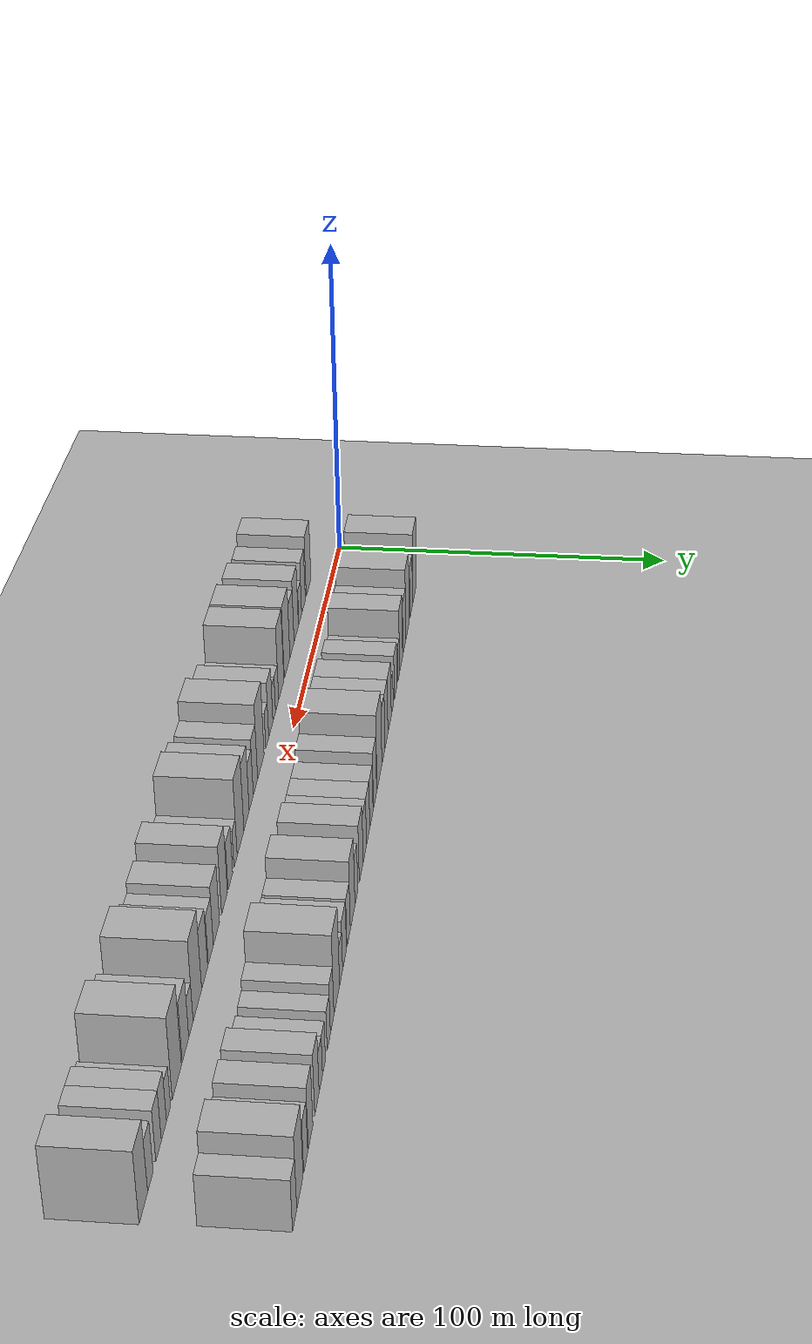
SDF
<?xml version="1.0" encoding="utf-8"?>

<sdf version="1.6">

   <world name="default">

      <gui fullscreen="0">

         <camera name="user_camera">

            <pose>-15 0 4.57585 0 0 0</pose>

            <view_controller>orbit</view_controller>

         </camera>

      </gui>

      <scene>

         <sky>

           <clouds>

             <speed>12</speed>

           </clouds>

         </sky>

         <ambient>0.4 0.4 0.4 1</ambient>

         <background>0.7 0.7 0.7 1</background>

         <shadows>1</shadows>

      </scene>

      <gravity>0 0 -9.8066</gravity>

      <magnetic_field>6e-06 2.3e-05 -4.2e-05</magnetic_field>

      <physics default="0" name="default_physics" type="ode">

         <ode>

            <solver>

               <type>quick</type>

               <iters>10</iters>

               <sor>1.0</sor>

               <use_dynamic_moi_rescaling>0</use_dynamic_moi_rescaling>

            </solver>

            <constraints>

               <cfm>0</cfm>

               <erp>0.2</erp>

               <contact_max_correcting_vel>100</contact_max_correcting_vel>

               <contact_surface_layer>0.001</contact_surface_layer>

            </constraints>

         </ode>

         <max_step_size>0.004</max_step_size>

         <real_time_factor>1</real_time_factor>

         <real_time_update_rate>250</real_time_update_rate>

      </physics>

      <light name="sun" type="directional">

         <cast_shadows>1</cast_shadows>

         <pose>0 0 10 0 0 0</pose>

         <diffuse>0.8 0.8 0.8 1</diffuse>

         <specular>0.2 0.2 0.2 1</specular>

         <attenuation>

            <range>1000</range>

            <constant>0.9</constant>

            <linear>0.01</linear>

            <quadratic>0.001</quadratic>

         </attenuation>

         <direction>-0.5 0.1 -0.9</direction>

      </light>

      <include>

         <name>ground_plane_1</name>

         <uri>model://HANNAS_ground_plane</uri>

         <pose>0 0 0  0 0 0</pose>

      </include>

      <include>

         <name>ground_plane_2</name>

         <uri>model://HANNAS_ground_plane</uri>

         <pose>100 0 0  0 0 0</pose>

      </include>

      <model name="building_1">

         <static>1</static>

         <pose frame="">27.2932 16.0000 0 0.000000 0.000000 1.570796</pose>

         <link name="link">

            <pose frame="">0 0 12.00 0 0 0</pose>

            <collision name="collision">

               <geometry>

                  <box>

                     <size>20.0000 10.5864 24.0000</size>

                  </box>

               </geometry>

               <max_contacts>10</max_contacts>

               <surface>

                  <contact>

                     <ode/>

                  </contact>

                  <bounce/>

                  <friction>

                     <torsional>

                        <ode/>

                     </torsional>

                     <ode/>

                  </friction>

               </surface>

            </collision>

            <visual name="visual">

               <cast_shadows>0</cast_shadows>

               <geometry>

                  <box>

                     <size>20.0000 10.5864 24.0000</size>

                  </box>

               </geometry>

               <material>

                  <script>

                     <uri>model://HANNAS_wall/materials/scripts</uri>

                     <uri>model://HANNAS_wall/materials/textures</uri>

                     <name>vrc/HANNAS_wall</name>

                  </script>

               </material>

            </visual>

            <self_collide>0</self_collide>

            <enable_wind>0</enable_wind>

            <kinematic>0</kinematic>

         </link>

      </model>

      <model name="building_2">

         <static>1</static>

         <pose frame="">37.3709 16.0000 0 0.000000 0.000000 1.570796</pose>

         <link name="link">

            <pose frame="">0 0 9.00 0 0 0</pose>

            <collision name="collision">

               <geometry>

                  <box>

                     <size>20.0000 7.5691 18.0000</size>

                  </box>

               </geometry>

               <max_contacts>10</max_contacts>

               <surface>

                  <contact>

                     <ode/>

                  </contact>

                  <bounce/>

                  <friction>

                     <torsional>

                        <ode/>

                     </torsional>

                     <ode/>

                  </friction>

               </surface>

            </collision>

            <visual name="visual">

               <cast_shadows>0</cast_shadows>

               <geometry>

                  <box>

                     <size>20.0000 7.5691 18.0000</size>

                  </box>

               </geometry>

               <material>

                  <script>

                     <uri>model://HANNAS_wall/materials/scripts</uri>

                     <uri>model://HANNAS_wall/materials/textures</uri>

                     <name>vrc/HANNAS_wall</name>

                  </script>

               </material>

            </visual>

            <self_collide>0</self_collide>

            <enable_wind>0</enable_wind>

            <kinematic>0</kinematic>

         </link>

      </model>

      <model name="building_3">

         <static>1</static>

         <pose frame="">48.1267 16.0000 0 0.000000 0.000000 1.570796</pose>

         <link name="link">

            <pose frame="">0 0 12.00 0 0 0</pose>

            <collision name="collision">

               <geometry>

                  <box>

                     <size>20.0000 9.9425 24.0000</size>

                  </box>

               </geometry>

               <max_contacts>10</max_contacts>

               <surface>

                  <contact>

                     <ode/>

                  </contact>

                  <bounce/>

                  <friction>

                     <torsional>

                        <ode/>

                     </torsional>

                     <ode/>

                  </friction>

               </surface>

            </collision>

            <visual name="visual">

               <cast_shadows>0</cast_shadows>

               <geometry>

                  <box>

                     <size>20.0000 9.9425 24.0000</size>

                  </box>

               </geometry>

               <material>

                  <script>

                     <uri>model://HANNAS_wall/materials/scripts</uri>

                     <uri>model://HANNAS_wall/materials/textures</uri>

                     <name>vrc/HANNAS_wall</name>

                  </script>

               </material>

            </visual>

            <self_collide>0</self_collide>

            <enable_wind>0</enable_wind>

            <kinematic>0</kinematic>

         </link>

      </model>

      <model name="building_4">

         <static>1</static>

         <pose frame="">57.1038 16.0000 0 0.000000 0.000000 1.570796</pose>

         <link name="link">

            <pose frame="">0 0 9.00 0 0 0</pose>

            <collision name="collision">

               <geometry>

                  <box>

                     <size>20.0000 8.0115 18.0000</size>

                  </box>

               </geometry>

               <max_contacts>10</max_contacts>

               <surface>

                  <contact>

                     <ode/>

                  </contact>

                  <bounce/>

                  <friction>

                     <torsional>

                        <ode/>

                     </torsional>

                     <ode/>

                  </friction>

               </surface>

            </collision>

            <visual name="visual">

               <cast_shadows>0</cast_shadows>

               <geometry>

                  <box>

                     <size>20.0000 8.0115 18.0000</size>

                  </box>

               </geometry>

               <material>

                  <script>

                     <uri>model://HANNAS_wall/materials/scripts</uri>

                     <uri>model://HANNAS_wall/materials/textures</uri>

                     <name>vrc/HANNAS_wall</name>

                  </script>

               </material>

            </visual>

            <self_collide>0</self_collide>

            <enable_wind>0</enable_wind>

            <kinematic>0</kinematic>

         </link>

      </model>

      <model name="building_5">

         <static>1</static>

         <pose frame="">66.3488 16.0000 0 0.000000 0.000000 1.570796</pose>

         <link name="link">

            <pose frame="">0 0 10.50 0 0 0</pose>

            <collision name="collision">

               <geometry>

                  <box>

                     <size>20.0000 8.4785 21.0000</size>

                  </box>

               </geometry>

               <max_contacts>10</max_contacts>

               <surface>

                  <contact>

                     <ode/>

                  </contact>

                  <bounce/>

                  <friction>

                     <torsional>

                        <ode/>

                     </torsional>

                     <ode/>

                  </friction>

               </surface>

            </collision>

            <visual name="visual">

               <cast_shadows>0</cast_shadows>

               <geometry>

                  <box>

                     <size>20.0000 8.4785 21.0000</size>

                  </box>

               </geometry>

               <material>

                  <script>

                     <uri>model://HANNAS_wall/materials/scripts</uri>

                     <uri>model://HANNAS_wall/materials/textures</uri>

                     <name>vrc/HANNAS_wall</name>

                  </script>

               </material>

            </visual>

            <self_collide>0</self_collide>

            <enable_wind>0</enable_wind>

            <kinematic>0</kinematic>

         </link>

      </model>

      <model name="building_6">

         <static>1</static>

         <pose frame="">73.0693 16.0000 0 0.000000 0.000000 1.570796</pose>

         <link name="link">

            <pose frame="">0 0 6.00 0 0 0</pose>

            <collision name="collision">

               <geometry>

                  <box>

                     <size>20.0000 4.9626 12.0000</size>

                  </box>

               </geometry>

               <max_contacts>10</max_contacts>

               <surface>

                  <contact>

                     <ode/>

                  </contact>

                  <bounce/>

                  <friction>

                     <torsional>

                        <ode/>

                     </torsional>

                     <ode/>

                  </friction>

               </surface>

            </collision>

            <visual name="visual">

               <cast_shadows>0</cast_shadows>

               <geometry>

                  <box>

                     <size>20.0000 4.9626 12.0000</size>

                  </box>

               </geometry>

               <material>

                  <script>

                     <uri>model://HANNAS_wall/materials/scripts</uri>

                     <uri>model://HANNAS_wall/materials/textures</uri>

                     <name>vrc/HANNAS_wall</name>

                  </script>

               </material>

            </visual>

            <self_collide>0</self_collide>

            <enable_wind>0</enable_wind>

            <kinematic>0</kinematic>

         </link>

      </model>

      <model name="building_7">

         <static>1</static>

         <pose frame="">81.1387 16.0000 0 0.000000 0.000000 1.570796</pose>

         <link name="link">

            <pose frame="">0 0 7.50 0 0 0</pose>

            <collision name="collision">

               <geometry>

                  <box>

                     <size>20.0000 7.1761 15.0000</size>

                  </box>

               </geometry>

               <max_contacts>10</max_contacts>

               <surface>

                  <contact>

                     <ode/>

                  </contact>

                  <bounce/>

                  <friction>

                     <torsional>

                        <ode/>

                     </torsional>

                     <ode/>

                  </friction>

               </surface>

            </collision>

            <visual name="visual">

               <cast_shadows>0</cast_shadows>

               <geometry>

                  <box>

                     <size>20.0000 7.1761 15.0000</size>

                  </box>

               </geometry>

               <material>

                  <script>

                     <uri>model://HANNAS_wall/materials/scripts</uri>

                     <uri>model://HANNAS_wall/materials/textures</uri>

                     <name>vrc/HANNAS_wall</name>

                  </script>

               </material>

            </visual>

            <self_collide>0</self_collide>

            <enable_wind>0</enable_wind>

            <kinematic>0</kinematic>

         </link>

      </model>

      <model name="building_8">

         <static>1</static>

         <pose frame="">90.1643 16.0000 0 0.000000 0.000000 1.570796</pose>

         <link name="link">

            <pose frame="">0 0 6.00 0 0 0</pose>

            <collision name="collision">

               <geometry>

                  <box>

                     <size>20.0000 4.8752 12.0000</size>

                  </box>

               </geometry>

               <max_contacts>10</max_contacts>

               <surface>

                  <contact>

                     <ode/>

                  </contact>

                  <bounce/>

                  <friction>

                     <torsional>

                        <ode/>

                     </torsional>

                     <ode/>

                  </friction>

               </surface>

            </collision>

            <visual name="visual">

               <cast_shadows>0</cast_shadows>

               <geometry>

                  <box>

                     <size>20.0000 4.8752 12.0000</size>

                  </box>

               </geometry>

               <material>

                  <script>

                     <uri>model://HANNAS_wall/materials/scripts</uri>

                     <uri>model://HANNAS_wall/materials/textures</uri>

                     <name>vrc/HANNAS_wall</name>

                  </script>

               </material>

            </visual>

            <self_collide>0</self_collide>

            <enable_wind>0</enable_wind>

            <kinematic>0</kinematic>

         </link>

      </model>

      <model name="building_9">

         <static>1</static>

         <pose frame="">96.9765 16.0000 0 0.000000 0.000000 1.570796</pose>

         <link name="link">

            <pose frame="">0 0 9.00 0 0 0</pose>

            <collision name="collision">

               <geometry>

                  <box>

                     <size>20.0000 8.7492 18.0000</size>

                  </box>

               </geometry>

               <max_contacts>10</max_contacts>

               <surface>

                  <contact>

                     <ode/>

                  </contact>

                  <bounce/>

                  <friction>

                     <torsional>

                        <ode/>

                     </torsional>

                     <ode/>

                  </friction>

               </surface>

            </collision>

            <visual name="visual">

               <cast_shadows>0</cast_shadows>

               <geometry>

                  <box>

                     <size>20.0000 8.7492 18.0000</size>

                  </box>

               </geometry>

               <material>

                  <script>

                     <uri>model://HANNAS_wall/materials/scripts</uri>

                     <uri>model://HANNAS_wall/materials/textures</uri>

                     <name>vrc/HANNAS_wall</name>

                  </script>

               </material>

            </visual>

            <self_collide>0</self_collide>

            <enable_wind>0</enable_wind>

            <kinematic>0</kinematic>

         </link>

      </model>

      <model name="building_10">

         <static>1</static>

         <pose frame="">104.9557 16.0000 0 0.000000 0.000000 1.570796</pose>

         <link name="link">

            <pose frame="">0 0 9.00 0 0 0</pose>

            <collision name="collision">

               <geometry>

                  <box>

                     <size>20.0000 7.2093 18.0000</size>

                  </box>

               </geometry>

               <max_contacts>10</max_contacts>

               <surface>

                  <contact>

                     <ode/>

                  </contact>

                  <bounce/>

                  <friction>

                     <torsional>

                        <ode/>

                     </torsional>

                     <ode/>

                  </friction>

               </surface>

            </collision>

            <visual name="visual">

               <cast_shadows>0</cast_shadows>

               <geometry>

                  <box>

                     <size>20.0000 7.2093 18.0000</size>

                  </box>

               </geometry>

               <material>

                  <script>

                     <uri>model://HANNAS_wall/materials/scripts</uri>

                     <uri>model://HANNAS_wall/materials/textures</uri>

                     <name>vrc/HANNAS_wall</name>

                  </script>

               </material>

            </visual>

            <self_collide>0</self_collide>

            <enable_wind>0</enable_wind>

            <kinematic>0</kinematic>

         </link>

      </model>

      <model name="building_11">

         <static>1</static>

         <pose frame="">112.4397 16.0000 0 0.000000 0.000000 1.570796</pose>

         <link name="link">

            <pose frame="">0 0 9.00 0 0 0</pose>

            <collision name="collision">

               <geometry>

                  <box>

                     <size>20.0000 7.7585 18.0000</size>

                  </box>

               </geometry>

               <max_contacts>10</max_contacts>

               <surface>

                  <contact>

                     <ode/>

                  </contact>

                  <bounce/>

                  <friction>

                     <torsional>

                        <ode/>

                     </torsional>

                     <ode/>

                  </friction>

               </surface>

            </collision>

            <visual name="visual">

               <cast_shadows>0</cast_shadows>

               <geometry>

                  <box>

                     <size>20.0000 7.7585 18.0000</size>

                  </box>

               </geometry>

               <material>

                  <script>

                     <uri>model://HANNAS_wall/materials/scripts</uri>

                     <uri>model://HANNAS_wall/materials/textures</uri>

                     <name>vrc/HANNAS_wall</name>

                  </script>

               </material>

            </visual>

            <self_collide>0</self_collide>

            <enable_wind>0</enable_wind>

            <kinematic>0</kinematic>

         </link>

      </model>

      <model name="building_12">

         <static>1</static>

         <pose frame="">122.1237 16.0000 0 0.000000 0.000000 1.570796</pose>

         <link name="link">

            <pose frame="">0 0 12.00 0 0 0</pose>

            <collision name="collision">

               <geometry>

                  <box>

                     <size>20.0000 11.6096 24.0000</size>

                  </box>

               </geometry>

               <max_contacts>10</max_contacts>

               <surface>

                  <contact>

                     <ode/>

                  </contact>

                  <bounce/>

                  <friction>

                     <torsional>

                        <ode/>

                     </torsional>

                     <ode/>

                  </friction>

               </surface>

            </collision>

            <visual name="visual">

               <cast_shadows>0</cast_shadows>

               <geometry>

                  <box>

                     <size>20.0000 11.6096 24.0000</size>

                  </box>

               </geometry>

               <material>

                  <script>

                     <uri>model://HANNAS_wall/materials/scripts</uri>

                     <uri>model://HANNAS_wall/materials/textures</uri>

                     <name>vrc/HANNAS_wall</name>

                  </script>

               </material>

            </visual>

            <self_collide>0</self_collide>

            <enable_wind>0</enable_wind>

            <kinematic>0</kinematic>

         </link>

      </model>

      <model name="building_13">

         <static>1</static>

         <pose frame="">132.6092 16.0000 0 0.000000 0.000000 1.570796</pose>

         <link name="link">

            <pose frame="">0 0 9.00 0 0 0</pose>

            <collision name="collision">

               <geometry>

                  <box>

                     <size>20.0000 7.3614 18.0000</size>

                  </box>

               </geometry>

               <max_contacts>10</max_contacts>

               <surface>

                  <contact>

                     <ode/>

                  </contact>

                  <bounce/>

                  <friction>

                     <torsional>

                        <ode/>

                     </torsional>

                     <ode/>

                  </friction>

               </surface>

            </collision>

            <visual name="visual">

               <cast_shadows>0</cast_shadows>

               <geometry>

                  <box>

                     <size>20.0000 7.3614 18.0000</size>

                  </box>

               </geometry>

               <material>

                  <script>

                     <uri>model://HANNAS_wall/materials/scripts</uri>

                     <uri>model://HANNAS_wall/materials/textures</uri>

                     <name>vrc/HANNAS_wall</name>

                  </script>

               </material>

            </visual>

            <self_collide>0</self_collide>

            <enable_wind>0</enable_wind>

            <kinematic>0</kinematic>

         </link>

      </model>

      <model name="building_14">

         <static>1</static>

         <pose frame="">140.9955 16.0000 0 0.000000 0.000000 1.570796</pose>

         <link name="link">

            <pose frame="">0 0 7.50 0 0 0</pose>

            <collision name="collision">

               <geometry>

                  <box>

                     <size>20.0000 7.4113 15.0000</size>

                  </box>

               </geometry>

               <max_contacts>10</max_contacts>

               <surface>

                  <contact>

                     <ode/>

                  </contact>

                  <bounce/>

                  <friction>

                     <torsional>

                        <ode/>

                     </torsional>

                     <ode/>

                  </friction>

               </surface>

            </collision>

            <visual name="visual">

               <cast_shadows>0</cast_shadows>

               <geometry>

                  <box>

                     <size>20.0000 7.4113 15.0000</size>

                  </box>

               </geometry>

               <material>

                  <script>

                     <uri>model://HANNAS_wall/materials/scripts</uri>

                     <uri>model://HANNAS_wall/materials/textures</uri>

                     <name>vrc/HANNAS_wall</name>

                  </script>

               </material>

            </visual>

            <self_collide>0</self_collide>

            <enable_wind>0</enable_wind>

            <kinematic>0</kinematic>

         </link>

      </model>

      <model name="building_15">

         <static>1</static>

         <pose frame="">148.3670 16.0000 0 0.000000 0.000000 1.570796</pose>

         <link name="link">

            <pose frame="">0 0 7.50 0 0 0</pose>

            <collision name="collision">

               <geometry>

                  <box>

                     <size>20.0000 7.3316 15.0000</size>

                  </box>

               </geometry>

               <max_contacts>10</max_contacts>

               <surface>

                  <contact>

                     <ode/>

                  </contact>

                  <bounce/>

                  <friction>

                     <torsional>

                        <ode/>

                     </torsional>

                     <ode/>

                  </friction>

               </surface>

            </collision>

            <visual name="visual">

               <cast_shadows>0</cast_shadows>

               <geometry>

                  <box>

                     <size>20.0000 7.3316 15.0000</size>

                  </box>

               </geometry>

               <material>

                  <script>

                     <uri>model://HANNAS_wall/materials/scripts</uri>

                     <uri>model://HANNAS_wall/materials/textures</uri>

                     <name>vrc/HANNAS_wall</name>

                  </script>

               </material>

            </visual>

            <self_collide>0</self_collide>

            <enable_wind>0</enable_wind>

            <kinematic>0</kinematic>

         </link>

      </model>

      <model name="building_16">

         <static>1</static>

         <pose frame="">155.6822 16.0000 0 0.000000 0.000000 1.570796</pose>

         <link name="link">

            <pose frame="">0 0 7.50 0 0 0</pose>

            <collision name="collision">

               <geometry>

                  <box>

                     <size>20.0000 7.2989 15.0000</size>

                  </box>

               </geometry>

               <max_contacts>10</max_contacts>

               <surface>

                  <contact>

                     <ode/>

                  </contact>

                  <bounce/>

                  <friction>

                     <torsional>

                        <ode/>

                     </torsional>

                     <ode/>

                  </friction>

               </surface>

            </collision>

            <visual name="visual">

               <cast_shadows>0</cast_shadows>

               <geometry>

                  <box>

                     <size>20.0000 7.2989 15.0000</size>

                  </box>

               </geometry>

               <material>

                  <script>

                     <uri>model://HANNAS_wall/materials/scripts</uri>

                     <uri>model://HANNAS_wall/materials/textures</uri>

                     <name>vrc/HANNAS_wall</name>

                  </script>

               </material>

            </visual>

            <self_collide>0</self_collide>

            <enable_wind>0</enable_wind>

            <kinematic>0</kinematic>

         </link>

      </model>

      <model name="building_17">

         <static>1</static>

         <pose frame="">163.4981 16.0000 0 0.000000 0.000000 1.570796</pose>

         <link name="link">

            <pose frame="">0 0 9.00 0 0 0</pose>

            <collision name="collision">

               <geometry>

                  <box>

                     <size>20.0000 8.3329 18.0000</size>

                  </box>

               </geometry>

               <max_contacts>10</max_contacts>

               <surface>

                  <contact>

                     <ode/>

                  </contact>

                  <bounce/>

                  <friction>

                     <torsional>

                        <ode/>

                     </torsional>

                     <ode/>

                  </friction>

               </surface>

            </collision>

            <visual name="visual">

               <cast_shadows>0</cast_shadows>

               <geometry>

                  <box>

                     <size>20.0000 8.3329 18.0000</size>

                  </box>

               </geometry>

               <material>

                  <script>

                     <uri>model://HANNAS_wall/materials/scripts</uri>

                     <uri>model://HANNAS_wall/materials/textures</uri>

                     <name>vrc/HANNAS_wall</name>

                  </script>

               </material>

            </visual>

            <self_collide>0</self_collide>

            <enable_wind>0</enable_wind>

            <kinematic>0</kinematic>

         </link>

      </model>

      <model name="building_18">

         <static>1</static>

         <pose frame="">173.7253 16.0000 0 0.000000 0.000000 1.570796</pose>

         <link name="link">

            <pose frame="">0 0 7.50 0 0 0</pose>

            <collision name="collision">

               <geometry>

                  <box>

                     <size>20.0000 6.1214 15.0000</size>

                  </box>

               </geometry>

               <max_contacts>10</max_contacts>

               <surface>

                  <contact>

                     <ode/>

                  </contact>

                  <bounce/>

                  <friction>

                     <torsional>

                        <ode/>

                     </torsional>

                     <ode/>

                  </friction>

               </surface>

            </collision>

            <visual name="visual">

               <cast_shadows>0</cast_shadows>

               <geometry>

                  <box>

                     <size>20.0000 6.1214 15.0000</size>

                  </box>

               </geometry>

               <material>

                  <script>

                     <uri>model://HANNAS_wall/materials/scripts</uri>

                     <uri>model://HANNAS_wall/materials/textures</uri>

                     <name>vrc/HANNAS_wall</name>

                  </script>

               </material>

            </visual>

            <self_collide>0</self_collide>

            <enable_wind>0</enable_wind>

            <kinematic>0</kinematic>

         </link>

      </model>

      <model name="building_19">

         <static>1</static>

         <pose frame="">181.4577 16.0000 0 0.000000 0.000000 1.570796</pose>

         <link name="link">

            <pose frame="">0 0 10.50 0 0 0</pose>

            <collision name="collision">

               <geometry>

                  <box>

                     <size>20.0000 9.3434 21.0000</size>

                  </box>

               </geometry>

               <max_contacts>10</max_contacts>

               <surface>

                  <contact>

                     <ode/>

                  </contact>

                  <bounce/>

                  <friction>

                     <torsional>

                        <ode/>

                     </torsional>

                     <ode/>

                  </friction>

               </surface>

            </collision>

            <visual name="visual">

               <cast_shadows>0</cast_shadows>

               <geometry>

                  <box>

                     <size>20.0000 9.3434 21.0000</size>

                  </box>

               </geometry>

               <material>

                  <script>

                     <uri>model://HANNAS_wall/materials/scripts</uri>

                     <uri>model://HANNAS_wall/materials/textures</uri>

                     <name>vrc/HANNAS_wall</name>

                  </script>

               </material>

            </visual>

            <self_collide>0</self_collide>

            <enable_wind>0</enable_wind>

            <kinematic>0</kinematic>

         </link>

      </model>

      <model name="building_20">

         <static>1</static>

         <pose frame="">189.4932 16.0000 0 0.000000 0.000000 1.570796</pose>

         <link name="link">

            <pose frame="">0 0 7.50 0 0 0</pose>

            <collision name="collision">

               <geometry>

                  <box>

                     <size>20.0000 6.7278 15.0000</size>

                  </box>

               </geometry>

               <max_contacts>10</max_contacts>

               <surface>

                  <contact>

                     <ode/>

                  </contact>

                  <bounce/>

                  <friction>

                     <torsional>

                        <ode/>

                     </torsional>

                     <ode/>

                  </friction>

               </surface>

            </collision>

            <visual name="visual">

               <cast_shadows>0</cast_shadows>

               <geometry>

                  <box>

                     <size>20.0000 6.7278 15.0000</size>

                  </box>

               </geometry>

               <material>

                  <script>

                     <uri>model://HANNAS_wall/materials/scripts</uri>

                     <uri>model://HANNAS_wall/materials/textures</uri>

                     <name>vrc/HANNAS_wall</name>

                  </script>

               </material>

            </visual>

            <self_collide>0</self_collide>

            <enable_wind>0</enable_wind>

            <kinematic>0</kinematic>

         </link>

      </model>

      <model name="building_21">

         <static>1</static>

         <pose frame="">197.5822 16.0000 0 0.000000 0.000000 1.570796</pose>

         <link name="link">

            <pose frame="">0 0 7.50 0 0 0</pose>

            <collision name="collision">

               <geometry>

                  <box>

                     <size>20.0000 7.4502 15.0000</size>

                  </box>

               </geometry>

               <max_contacts>10</max_contacts>

               <surface>

                  <contact>

                     <ode/>

                  </contact>

                  <bounce/>

                  <friction>

                     <torsional>

                        <ode/>

                     </torsional>

                     <ode/>

                  </friction>

               </surface>

            </collision>

            <visual name="visual">

               <cast_shadows>0</cast_shadows>

               <geometry>

                  <box>

                     <size>20.0000 7.4502 15.0000</size>

                  </box>

               </geometry>

               <material>

                  <script>

                     <uri>model://HANNAS_wall/materials/scripts</uri>

                     <uri>model://HANNAS_wall/materials/textures</uri>

                     <name>vrc/HANNAS_wall</name>

                  </script>

               </material>

            </visual>

            <self_collide>0</self_collide>

            <enable_wind>0</enable_wind>

            <kinematic>0</kinematic>

         </link>

      </model>

      <model name="building_22">

         <static>1</static>

         <pose frame="">204.2305 16.0000 0 0.000000 0.000000 1.570796</pose>

         <link name="link">

            <pose frame="">0 0 6.00 0 0 0</pose>

            <collision name="collision">

               <geometry>

                  <box>

                     <size>20.0000 5.8465 12.0000</size>

                  </box>

               </geometry>

               <max_contacts>10</max_contacts>

               <surface>

                  <contact>

                     <ode/>

                  </contact>

                  <bounce/>

                  <friction>

                     <torsional>

                        <ode/>

                     </torsional>

                     <ode/>

                  </friction>

               </surface>

            </collision>

            <visual name="visual">

               <cast_shadows>0</cast_shadows>

               <geometry>

                  <box>

                     <size>20.0000 5.8465 12.0000</size>

                  </box>

               </geometry>

               <material>

                  <script>

                     <uri>model://HANNAS_wall/materials/scripts</uri>

                     <uri>model://HANNAS_wall/materials/textures</uri>

                     <name>vrc/HANNAS_wall</name>

                  </script>

               </material>

            </visual>

            <self_collide>0</self_collide>

            <enable_wind>0</enable_wind>

            <kinematic>0</kinematic>

         </link>

      </model>

      <model name="building_23">

         <static>1</static>

         <pose frame="">212.3700 16.0000 0 0.000000 0.000000 1.570796</pose>

         <link name="link">

            <pose frame="">0 0 12.00 0 0 0</pose>

            <collision name="collision">

               <geometry>

                  <box>

                     <size>20.0000 10.4324 24.0000</size>

                  </box>

               </geometry>

               <max_contacts>10</max_contacts>

               <surface>

                  <contact>

                     <ode/>

                  </contact>

                  <bounce/>

                  <friction>

                     <torsional>

                        <ode/>

                     </torsional>

                     <ode/>

                  </friction>

               </surface>

            </collision>

            <visual name="visual">

               <cast_shadows>0</cast_shadows>

               <geometry>

                  <box>

                     <size>20.0000 10.4324 24.0000</size>

                  </box>

               </geometry>

               <material>

                  <script>

                     <uri>model://HANNAS_wall/materials/scripts</uri>

                     <uri>model://HANNAS_wall/materials/textures</uri>

                     <name>vrc/HANNAS_wall</name>

                  </script>

               </material>

            </visual>

            <self_collide>0</self_collide>

            <enable_wind>0</enable_wind>

            <kinematic>0</kinematic>

         </link>

      </model>

      <model name="building_24">

         <static>1</static>

         <pose frame="">220.7596 16.0000 0 0.000000 0.000000 1.570796</pose>

         <link name="link">

            <pose frame="">0 0 7.50 0 0 0</pose>

            <collision name="collision">

               <geometry>

                  <box>

                     <size>20.0000 6.3466 15.0000</size>

                  </box>

               </geometry>

               <max_contacts>10</max_contacts>

               <surface>

                  <contact>

                     <ode/>

                  </contact>

                  <bounce/>

                  <friction>

                     <torsional>

                        <ode/>

                     </torsional>

                     <ode/>

                  </friction>

               </surface>

            </collision>

            <visual name="visual">

               <cast_shadows>0</cast_shadows>

               <geometry>

                  <box>

                     <size>20.0000 6.3466 15.0000</size>

                  </box>

               </geometry>

               <material>

                  <script>

                     <uri>model://HANNAS_wall/materials/scripts</uri>

                     <uri>model://HANNAS_wall/materials/textures</uri>

                     <name>vrc/HANNAS_wall</name>

                  </script>

               </material>

            </visual>

            <self_collide>0</self_collide>

            <enable_wind>0</enable_wind>

            <kinematic>0</kinematic>

         </link>

      </model>

      <model name="building_25">

         <static>1</static>

         <pose frame="">226.8524 16.0000 0 0.000000 0.000000 1.570796</pose>

         <link name="link">

            <pose frame="">0 0 6.00 0 0 0</pose>

            <collision name="collision">

               <geometry>

                  <box>

                     <size>20.0000 5.8391 12.0000</size>

                  </box>

               </geometry>

               <max_contacts>10</max_contacts>

               <surface>

                  <contact>

                     <ode/>

                  </contact>

                  <bounce/>

                  <friction>

                     <torsional>

                        <ode/>

                     </torsional>

                     <ode/>

                  </friction>

               </surface>

            </collision>

            <visual name="visual">

               <cast_shadows>0</cast_shadows>

               <geometry>

                  <box>

                     <size>20.0000 5.8391 12.0000</size>

                  </box>

               </geometry>

               <material>

                  <script>

                     <uri>model://HANNAS_wall/materials/scripts</uri>

                     <uri>model://HANNAS_wall/materials/textures</uri>

                     <name>vrc/HANNAS_wall</name>

                  </script>

               </material>

            </visual>

            <self_collide>0</self_collide>

            <enable_wind>0</enable_wind>

            <kinematic>0</kinematic>

         </link>

      </model>

      <model name="building_26">

         <static>1</static>

         <pose frame="">235.2844 16.0000 0 0.000000 0.000000 1.570796</pose>

         <link name="link">

            <pose frame="">0 0 6.00 0 0 0</pose>

            <collision name="collision">

               <geometry>

                  <box>

                     <size>20.0000 5.0248 12.0000</size>

                  </box>

               </geometry>

               <max_contacts>10</max_contacts>

               <surface>

                  <contact>

                     <ode/>

                  </contact>

                  <bounce/>

                  <friction>

                     <torsional>

                        <ode/>

                     </torsional>

                     <ode/>

                  </friction>

               </surface>

            </collision>

            <visual name="visual">

               <cast_shadows>0</cast_shadows>

               <geometry>

                  <box>

                     <size>20.0000 5.0248 12.0000</size>

                  </box>

               </geometry>

               <material>

                  <script>

                     <uri>model://HANNAS_wall/materials/scripts</uri>

                     <uri>model://HANNAS_wall/materials/textures</uri>

                     <name>vrc/HANNAS_wall</name>

                  </script>

               </material>

            </visual>

            <self_collide>0</self_collide>

            <enable_wind>0</enable_wind>

            <kinematic>0</kinematic>

         </link>

      </model>

      <model name="building_27">

         <static>1</static>

         <pose frame="">240.6908 16.0000 0 0.000000 0.000000 1.570796</pose>

         <link name="link">

            <pose frame="">0 0 6.00 0 0 0</pose>

            <collision name="collision">

               <geometry>

                  <box>

                     <size>20.0000 5.7879 12.0000</size>

                  </box>

               </geometry>

               <max_contacts>10</max_contacts>

               <surface>

                  <contact>

                     <ode/>

                  </contact>

                  <bounce/>

                  <friction>

                     <torsional>

                        <ode/>

                     </torsional>

                     <ode/>

                  </friction>

               </surface>

            </collision>

            <visual name="visual">

               <cast_shadows>0</cast_shadows>

               <geometry>

                  <box>

                     <size>20.0000 5.7879 12.0000</size>

                  </box>

               </geometry>

               <material>

                  <script>

                     <uri>model://HANNAS_wall/materials/scripts</uri>

                     <uri>model://HANNAS_wall/materials/textures</uri>

                     <name>vrc/HANNAS_wall</name>

                  </script>

               </material>

            </visual>

            <self_collide>0</self_collide>

            <enable_wind>0</enable_wind>

            <kinematic>0</kinematic>

         </link>

      </model>

      <model name="building_28">

         <static>1</static>

         <pose frame="">247.2457 16.0000 0 0.000000 0.000000 1.570796</pose>

         <link name="link">

            <pose frame="">0 0 9.00 0 0 0</pose>

            <collision name="collision">

               <geometry>

                  <box>

                     <size>20.0000 7.3219 18.0000</size>

                  </box>

               </geometry>

               <max_contacts>10</max_contacts>

               <surface>

                  <contact>

                     <ode/>

                  </contact>

                  <bounce/>

                  <friction>

                     <torsional>

                        <ode/>

                     </torsional>

                     <ode/>

                  </friction>

               </surface>

            </collision>

            <visual name="visual">

               <cast_shadows>0</cast_shadows>

               <geometry>

                  <box>

                     <size>20.0000 7.3219 18.0000</size>

                  </box>

               </geometry>

               <material>

                  <script>

                     <uri>model://HANNAS_wall/materials/scripts</uri>

                     <uri>model://HANNAS_wall/materials/textures</uri>

                     <name>vrc/HANNAS_wall</name>

                  </script>

               </material>

            </visual>

            <self_collide>0</self_collide>

            <enable_wind>0</enable_wind>

            <kinematic>0</kinematic>

         </link>

      </model>

      <model name="building_29">

         <static>1</static>

         <pose frame="">257.5737 16.0000 0 0.000000 0.000000 1.570796</pose>

         <link name="link">

            <pose frame="">0 0 9.00 0 0 0</pose>

            <collision name="collision">

               <geometry>

                  <box>

                     <size>20.0000 7.3342 18.0000</size>

                  </box>

               </geometry>

               <max_contacts>10</max_contacts>

               <surface>

                  <contact>

                     <ode/>

                  </contact>

                  <bounce/>

                  <friction>

                     <torsional>

                        <ode/>

                     </torsional>

                     <ode/>

                  </friction>

               </surface>

            </collision>

            <visual name="visual">

               <cast_shadows>0</cast_shadows>

               <geometry>

                  <box>

                     <size>20.0000 7.3342 18.0000</size>

                  </box>

               </geometry>

               <material>

                  <script>

                     <uri>model://HANNAS_wall/materials/scripts</uri>

                     <uri>model://HANNAS_wall/materials/textures</uri>

                     <name>vrc/HANNAS_wall</name>

                  </script>

               </material>

            </visual>

            <self_collide>0</self_collide>

            <enable_wind>0</enable_wind>

            <kinematic>0</kinematic>

         </link>

      </model>

      <model name="building_30">

         <static>1</static>

         <pose frame="">265.3771 16.0000 0 0.000000 0.000000 1.570796</pose>

         <link name="link">

            <pose frame="">0 0 7.50 0 0 0</pose>

            <collision name="collision">

               <geometry>

                  <box>

                     <size>20.0000 6.2727 15.0000</size>

                  </box>

               </geometry>

               <max_contacts>10</max_contacts>

               <surface>

                  <contact>

                     <ode/>

                  </contact>

                  <bounce/>

                  <friction>

                     <torsional>

                        <ode/>

                     </torsional>

                     <ode/>

                  </friction>

               </surface>

            </collision>

            <visual name="visual">

               <cast_shadows>0</cast_shadows>

               <geometry>

                  <box>

                     <size>20.0000 6.2727 15.0000</size>

                  </box>

               </geometry>

               <material>

                  <script>

                     <uri>model://HANNAS_wall/materials/scripts</uri>

                     <uri>model://HANNAS_wall/materials/textures</uri>

                     <name>vrc/HANNAS_wall</name>

                  </script>

               </material>

            </visual>

            <self_collide>0</self_collide>

            <enable_wind>0</enable_wind>

            <kinematic>0</kinematic>

         </link>

      </model>

      <model name="building_31">

         <static>1</static>

         <pose frame="">274.3056 16.0000 0 0.000000 0.000000 1.570796</pose>

         <link name="link">

            <pose frame="">0 0 10.50 0 0 0</pose>

            <collision name="collision">

               <geometry>

                  <box>

                     <size>20.0000 9.5843 21.0000</size>

                  </box>

               </geometry>

               <max_contacts>10</max_contacts>

               <surface>

                  <contact>

                     <ode/>

                  </contact>

                  <bounce/>

                  <friction>

                     <torsional>

                        <ode/>

                     </torsional>

                     <ode/>

                  </friction>

               </surface>

            </collision>

            <visual name="visual">

               <cast_shadows>0</cast_shadows>

               <geometry>

                  <box>

                     <size>20.0000 9.5843 21.0000</size>

                  </box>

               </geometry>

               <material>

                  <script>

                     <uri>model://HANNAS_wall/materials/scripts</uri>

                     <uri>model://HANNAS_wall/materials/textures</uri>

                     <name>vrc/HANNAS_wall</name>

                  </script>

               </material>

            </visual>

            <self_collide>0</self_collide>

            <enable_wind>0</enable_wind>

            <kinematic>0</kinematic>

         </link>

      </model>

      <model name="building_32">

         <static>1</static>

         <pose frame="">282.2590 16.0000 0 0.000000 0.000000 1.570796</pose>

         <link name="link">

            <pose frame="">0 0 7.50 0 0 0</pose>

            <collision name="collision">

               <geometry>

                  <box>

                     <size>20.0000 6.3225 15.0000</size>

                  </box>

               </geometry>

               <max_contacts>10</max_contacts>

               <surface>

                  <contact>

                     <ode/>

                  </contact>

                  <bounce/>

                  <friction>

                     <torsional>

                        <ode/>

                     </torsional>

                     <ode/>

                  </friction>

               </surface>

            </collision>

            <visual name="visual">

               <cast_shadows>0</cast_shadows>

               <geometry>

                  <box>

                     <size>20.0000 6.3225 15.0000</size>

                  </box>

               </geometry>

               <material>

                  <script>

                     <uri>model://HANNAS_wall/materials/scripts</uri>

                     <uri>model://HANNAS_wall/materials/textures</uri>

                     <name>vrc/HANNAS_wall</name>

                  </script>

               </material>

            </visual>

            <self_collide>0</self_collide>

            <enable_wind>0</enable_wind>

            <kinematic>0</kinematic>

         </link>

      </model>

      <model name="building_33">

         <static>1</static>

         <pose frame="">26.1225 -16.0000 0 0.000000 0.000000 1.570796</pose>

         <link name="link">

            <pose frame="">0 0 10.50 0 0 0</pose>

            <collision name="collision">

               <geometry>

                  <box>

                     <size>20.0000 10.2451 21.0000</size>

                  </box>

               </geometry>

               <max_contacts>10</max_contacts>

               <surface>

                  <contact>

                     <ode/>

                  </contact>

                  <bounce/>

                  <friction>

                     <torsional>

                        <ode/>

                     </torsional>

                     <ode/>

                  </friction>

               </surface>

            </collision>

            <visual name="visual">

               <cast_shadows>0</cast_shadows>

               <geometry>

                  <box>

                     <size>20.0000 10.2451 21.0000</size>

                  </box>

               </geometry>

               <material>

                  <script>

                     <uri>model://HANNAS_wall/materials/scripts</uri>

                     <uri>model://HANNAS_wall/materials/textures</uri>

                     <name>vrc/HANNAS_wall</name>

                  </script>

               </material>

            </visual>

            <self_collide>0</self_collide>

            <enable_wind>0</enable_wind>

            <kinematic>0</kinematic>

         </link>

      </model>

      <model name="building_34">

         <static>1</static>

         <pose frame="">37.2022 -16.0000 0 0.000000 0.000000 1.570796</pose>

         <link name="link">

            <pose frame="">0 0 9.00 0 0 0</pose>

            <collision name="collision">

               <geometry>

                  <box>

                     <size>20.0000 7.9142 18.0000</size>

                  </box>

               </geometry>

               <max_contacts>10</max_contacts>

               <surface>

                  <contact>

                     <ode/>

                  </contact>

                  <bounce/>

                  <friction>

                     <torsional>

                        <ode/>

                     </torsional>

                     <ode/>

                  </friction>

               </surface>

            </collision>

            <visual name="visual">

               <cast_shadows>0</cast_shadows>

               <geometry>

                  <box>

                     <size>20.0000 7.9142 18.0000</size>

                  </box>

               </geometry>

               <material>

                  <script>

                     <uri>model://HANNAS_wall/materials/scripts</uri>

                     <uri>model://HANNAS_wall/materials/textures</uri>

                     <name>vrc/HANNAS_wall</name>

                  </script>

               </material>

            </visual>

            <self_collide>0</self_collide>

            <enable_wind>0</enable_wind>

            <kinematic>0</kinematic>

         </link>

      </model>

      <model name="building_35">

         <static>1</static>

         <pose frame="">44.0995 -16.0000 0 0.000000 0.000000 1.570796</pose>

         <link name="link">

            <pose frame="">0 0 6.00 0 0 0</pose>

            <collision name="collision">

               <geometry>

                  <box>

                     <size>20.0000 5.8806 12.0000</size>

                  </box>

               </geometry>

               <max_contacts>10</max_contacts>

               <surface>

                  <contact>

                     <ode/>

                  </contact>

                  <bounce/>

                  <friction>

                     <torsional>

                        <ode/>

                     </torsional>

                     <ode/>

                  </friction>

               </surface>

            </collision>

            <visual name="visual">

               <cast_shadows>0</cast_shadows>

               <geometry>

                  <box>

                     <size>20.0000 5.8806 12.0000</size>

                  </box>

               </geometry>

               <material>

                  <script>

                     <uri>model://HANNAS_wall/materials/scripts</uri>

                     <uri>model://HANNAS_wall/materials/textures</uri>

                     <name>vrc/HANNAS_wall</name>

                  </script>

               </material>

            </visual>

            <self_collide>0</self_collide>

            <enable_wind>0</enable_wind>

            <kinematic>0</kinematic>

         </link>

      </model>

      <model name="building_36">

         <static>1</static>

         <pose frame="">52.5034 -16.0000 0 0.000000 0.000000 1.570796</pose>

         <link name="link">

            <pose frame="">0 0 10.50 0 0 0</pose>

            <collision name="collision">

               <geometry>

                  <box>

                     <size>20.0000 8.9273 21.0000</size>

                  </box>

               </geometry>

               <max_contacts>10</max_contacts>

               <surface>

                  <contact>

                     <ode/>

                  </contact>

                  <bounce/>

                  <friction>

                     <torsional>

                        <ode/>

                     </torsional>

                     <ode/>

                  </friction>

               </surface>

            </collision>

            <visual name="visual">

               <cast_shadows>0</cast_shadows>

               <geometry>

                  <box>

                     <size>20.0000 8.9273 21.0000</size>

                  </box>

               </geometry>

               <material>

                  <script>

                     <uri>model://HANNAS_wall/materials/scripts</uri>

                     <uri>model://HANNAS_wall/materials/textures</uri>

                     <name>vrc/HANNAS_wall</name>

                  </script>

               </material>

            </visual>

            <self_collide>0</self_collide>

            <enable_wind>0</enable_wind>

            <kinematic>0</kinematic>

         </link>

      </model>

      <model name="building_37">

         <static>1</static>

         <pose frame="">61.1999 -16.0000 0 0.000000 0.000000 1.570796</pose>

         <link name="link">

            <pose frame="">0 0 9.00 0 0 0</pose>

            <collision name="collision">

               <geometry>

                  <box>

                     <size>20.0000 8.4656 18.0000</size>

                  </box>

               </geometry>

               <max_contacts>10</max_contacts>

               <surface>

                  <contact>

                     <ode/>

                  </contact>

                  <bounce/>

                  <friction>

                     <torsional>

                        <ode/>

                     </torsional>

                     <ode/>

                  </friction>

               </surface>

            </collision>

            <visual name="visual">

               <cast_shadows>0</cast_shadows>

               <geometry>

                  <box>

                     <size>20.0000 8.4656 18.0000</size>

                  </box>

               </geometry>

               <material>

                  <script>

                     <uri>model://HANNAS_wall/materials/scripts</uri>

                     <uri>model://HANNAS_wall/materials/textures</uri>

                     <name>vrc/HANNAS_wall</name>

                  </script>

               </material>

            </visual>

            <self_collide>0</self_collide>

            <enable_wind>0</enable_wind>

            <kinematic>0</kinematic>

         </link>

      </model>

      <model name="building_38">

         <static>1</static>

         <pose frame="">70.9779 -16.0000 0 0.000000 0.000000 1.570796</pose>

         <link name="link">

            <pose frame="">0 0 12.00 0 0 0</pose>

            <collision name="collision">

               <geometry>

                  <box>

                     <size>20.0000 11.0904 24.0000</size>

                  </box>

               </geometry>

               <max_contacts>10</max_contacts>

               <surface>

                  <contact>

                     <ode/>

                  </contact>

                  <bounce/>

                  <friction>

                     <torsional>

                        <ode/>

                     </torsional>

                     <ode/>

                  </friction>

               </surface>

            </collision>

            <visual name="visual">

               <cast_shadows>0</cast_shadows>

               <geometry>

                  <box>

                     <size>20.0000 11.0904 24.0000</size>

                  </box>

               </geometry>

               <material>

                  <script>

                     <uri>model://HANNAS_wall/materials/scripts</uri>

                     <uri>model://HANNAS_wall/materials/textures</uri>

                     <name>vrc/HANNAS_wall</name>

                  </script>

               </material>

            </visual>

            <self_collide>0</self_collide>

            <enable_wind>0</enable_wind>

            <kinematic>0</kinematic>

         </link>

      </model>

      <model name="building_39">

         <static>1</static>

         <pose frame="">82.4978 -16.0000 0 0.000000 0.000000 1.570796</pose>

         <link name="link">

            <pose frame="">0 0 12.00 0 0 0</pose>

            <collision name="collision">

               <geometry>

                  <box>

                     <size>20.0000 9.9492 24.0000</size>

                  </box>

               </geometry>

               <max_contacts>10</max_contacts>

               <surface>

                  <contact>

                     <ode/>

                  </contact>

                  <bounce/>

                  <friction>

                     <torsional>

                        <ode/>

                     </torsional>

                     <ode/>

                  </friction>

               </surface>

            </collision>

            <visual name="visual">

               <cast_shadows>0</cast_shadows>

               <geometry>

                  <box>

                     <size>20.0000 9.9492 24.0000</size>

                  </box>

               </geometry>

               <material>

                  <script>

                     <uri>model://HANNAS_wall/materials/scripts</uri>

                     <uri>model://HANNAS_wall/materials/textures</uri>

                     <name>vrc/HANNAS_wall</name>

                  </script>

               </material>

            </visual>

            <self_collide>0</self_collide>

            <enable_wind>0</enable_wind>

            <kinematic>0</kinematic>

         </link>

      </model>

      <model name="building_40">

         <static>1</static>

         <pose frame="">90.4262 -16.0000 0 0.000000 0.000000 1.570796</pose>

         <link name="link">

            <pose frame="">0 0 6.00 0 0 0</pose>

            <collision name="collision">

               <geometry>

                  <box>

                     <size>20.0000 5.9077 12.0000</size>

                  </box>

               </geometry>

               <max_contacts>10</max_contacts>

               <surface>

                  <contact>

                     <ode/>

                  </contact>

                  <bounce/>

                  <friction>

                     <torsional>

                        <ode/>

                     </torsional>

                     <ode/>

                  </friction>

               </surface>

            </collision>

            <visual name="visual">

               <cast_shadows>0</cast_shadows>

               <geometry>

                  <box>

                     <size>20.0000 5.9077 12.0000</size>

                  </box>

               </geometry>

               <material>

                  <script>

                     <uri>model://HANNAS_wall/materials/scripts</uri>

                     <uri>model://HANNAS_wall/materials/textures</uri>

                     <name>vrc/HANNAS_wall</name>

                  </script>

               </material>

            </visual>

            <self_collide>0</self_collide>

            <enable_wind>0</enable_wind>

            <kinematic>0</kinematic>

         </link>

      </model>

      <model name="building_41">

         <static>1</static>

         <pose frame="">95.8811 -16.0000 0 0.000000 0.000000 1.570796</pose>

         <link name="link">

            <pose frame="">0 0 6.00 0 0 0</pose>

            <collision name="collision">

               <geometry>

                  <box>

                     <size>20.0000 5.0021 12.0000</size>

                  </box>

               </geometry>

               <max_contacts>10</max_contacts>

               <surface>

                  <contact>

                     <ode/>

                  </contact>

                  <bounce/>

                  <friction>

                     <torsional>

                        <ode/>

                     </torsional>

                     <ode/>

                  </friction>

               </surface>

            </collision>

            <visual name="visual">

               <cast_shadows>0</cast_shadows>

               <geometry>

                  <box>

                     <size>20.0000 5.0021 12.0000</size>

                  </box>

               </geometry>

               <material>

                  <script>

                     <uri>model://HANNAS_wall/materials/scripts</uri>

                     <uri>model://HANNAS_wall/materials/textures</uri>

                     <name>vrc/HANNAS_wall</name>

                  </script>

               </material>

            </visual>

            <self_collide>0</self_collide>

            <enable_wind>0</enable_wind>

            <kinematic>0</kinematic>

         </link>

      </model>

      <model name="building_42">

         <static>1</static>

         <pose frame="">102.1635 -16.0000 0 0.000000 0.000000 1.570796</pose>

         <link name="link">

            <pose frame="">0 0 9.00 0 0 0</pose>

            <collision name="collision">

               <geometry>

                  <box>

                     <size>20.0000 7.5627 18.0000</size>

                  </box>

               </geometry>

               <max_contacts>10</max_contacts>

               <surface>

                  <contact>

                     <ode/>

                  </contact>

                  <bounce/>

                  <friction>

                     <torsional>

                        <ode/>

                     </torsional>

                     <ode/>

                  </friction>

               </surface>

            </collision>

            <visual name="visual">

               <cast_shadows>0</cast_shadows>

               <geometry>

                  <box>

                     <size>20.0000 7.5627 18.0000</size>

                  </box>

               </geometry>

               <material>

                  <script>

                     <uri>model://HANNAS_wall/materials/scripts</uri>

                     <uri>model://HANNAS_wall/materials/textures</uri>

                     <name>vrc/HANNAS_wall</name>

                  </script>

               </material>

            </visual>

            <self_collide>0</self_collide>

            <enable_wind>0</enable_wind>

            <kinematic>0</kinematic>

         </link>

      </model>

      <model name="building_43">

         <static>1</static>

         <pose frame="">108.6462 -16.0000 0 0.000000 0.000000 1.570796</pose>

         <link name="link">

            <pose frame="">0 0 6.00 0 0 0</pose>

            <collision name="collision">

               <geometry>

                  <box>

                     <size>20.0000 5.4026 12.0000</size>

                  </box>

               </geometry>

               <max_contacts>10</max_contacts>

               <surface>

                  <contact>

                     <ode/>

                  </contact>

                  <bounce/>

                  <friction>

                     <torsional>

                        <ode/>

                     </torsional>

                     <ode/>

                  </friction>

               </surface>

            </collision>

            <visual name="visual">

               <cast_shadows>0</cast_shadows>

               <geometry>

                  <box>

                     <size>20.0000 5.4026 12.0000</size>

                  </box>

               </geometry>

               <material>

                  <script>

                     <uri>model://HANNAS_wall/materials/scripts</uri>

                     <uri>model://HANNAS_wall/materials/textures</uri>

                     <name>vrc/HANNAS_wall</name>

                  </script>

               </material>

            </visual>

            <self_collide>0</self_collide>

            <enable_wind>0</enable_wind>

            <kinematic>0</kinematic>

         </link>

      </model>

      <model name="building_44">

         <static>1</static>

         <pose frame="">119.9620 -16.0000 0 0.000000 0.000000 1.570796</pose>

         <link name="link">

            <pose frame="">0 0 12.00 0 0 0</pose>

            <collision name="collision">

               <geometry>

                  <box>

                     <size>20.0000 11.2290 24.0000</size>

                  </box>

               </geometry>

               <max_contacts>10</max_contacts>

               <surface>

                  <contact>

                     <ode/>

                  </contact>

                  <bounce/>

                  <friction>

                     <torsional>

                        <ode/>

                     </torsional>

                     <ode/>

                  </friction>

               </surface>

            </collision>

            <visual name="visual">

               <cast_shadows>0</cast_shadows>

               <geometry>

                  <box>

                     <size>20.0000 11.2290 24.0000</size>

                  </box>

               </geometry>

               <material>

                  <script>

                     <uri>model://HANNAS_wall/materials/scripts</uri>

                     <uri>model://HANNAS_wall/materials/textures</uri>

                     <name>vrc/HANNAS_wall</name>

                  </script>

               </material>

            </visual>

            <self_collide>0</self_collide>

            <enable_wind>0</enable_wind>

            <kinematic>0</kinematic>

         </link>

      </model>

      <model name="building_45">

         <static>1</static>

         <pose frame="">129.2773 -16.0000 0 0.000000 0.000000 1.570796</pose>

         <link name="link">

            <pose frame="">0 0 9.00 0 0 0</pose>

            <collision name="collision">

               <geometry>

                  <box>

                     <size>20.0000 7.4016 18.0000</size>

                  </box>

               </geometry>

               <max_contacts>10</max_contacts>

               <surface>

                  <contact>

                     <ode/>

                  </contact>

                  <bounce/>

                  <friction>

                     <torsional>

                        <ode/>

                     </torsional>

                     <ode/>

                  </friction>

               </surface>

            </collision>

            <visual name="visual">

               <cast_shadows>0</cast_shadows>

               <geometry>

                  <box>

                     <size>20.0000 7.4016 18.0000</size>

                  </box>

               </geometry>

               <material>

                  <script>

                     <uri>model://HANNAS_wall/materials/scripts</uri>

                     <uri>model://HANNAS_wall/materials/textures</uri>

                     <name>vrc/HANNAS_wall</name>

                  </script>

               </material>

            </visual>

            <self_collide>0</self_collide>

            <enable_wind>0</enable_wind>

            <kinematic>0</kinematic>

         </link>

      </model>

      <model name="building_46">

         <static>1</static>

         <pose frame="">136.4306 -16.0000 0 0.000000 0.000000 1.570796</pose>

         <link name="link">

            <pose frame="">0 0 7.50 0 0 0</pose>

            <collision name="collision">

               <geometry>

                  <box>

                     <size>20.0000 6.9052 15.0000</size>

                  </box>

               </geometry>

               <max_contacts>10</max_contacts>

               <surface>

                  <contact>

                     <ode/>

                  </contact>

                  <bounce/>

                  <friction>

                     <torsional>

                        <ode/>

                     </torsional>

                     <ode/>

                  </friction>

               </surface>

            </collision>

            <visual name="visual">

               <cast_shadows>0</cast_shadows>

               <geometry>

                  <box>

                     <size>20.0000 6.9052 15.0000</size>

                  </box>

               </geometry>

               <material>

                  <script>

                     <uri>model://HANNAS_wall/materials/scripts</uri>

                     <uri>model://HANNAS_wall/materials/textures</uri>

                     <name>vrc/HANNAS_wall</name>

                  </script>

               </material>

            </visual>

            <self_collide>0</self_collide>

            <enable_wind>0</enable_wind>

            <kinematic>0</kinematic>

         </link>

      </model>

      <model name="building_47">

         <static>1</static>

         <pose frame="">144.2147 -16.0000 0 0.000000 0.000000 1.570796</pose>

         <link name="link">

            <pose frame="">0 0 10.50 0 0 0</pose>

            <collision name="collision">

               <geometry>

                  <box>

                     <size>20.0000 8.6629 21.0000</size>

                  </box>

               </geometry>

               <max_contacts>10</max_contacts>

               <surface>

                  <contact>

                     <ode/>

                  </contact>

                  <bounce/>

                  <friction>

                     <torsional>

                        <ode/>

                     </torsional>

                     <ode/>

                  </friction>

               </surface>

            </collision>

            <visual name="visual">

               <cast_shadows>0</cast_shadows>

               <geometry>

                  <box>

                     <size>20.0000 8.6629 21.0000</size>

                  </box>

               </geometry>

               <material>

                  <script>

                     <uri>model://HANNAS_wall/materials/scripts</uri>

                     <uri>model://HANNAS_wall/materials/textures</uri>

                     <name>vrc/HANNAS_wall</name>

                  </script>

               </material>

            </visual>

            <self_collide>0</self_collide>

            <enable_wind>0</enable_wind>

            <kinematic>0</kinematic>

         </link>

      </model>

      <model name="building_48">

         <static>1</static>

         <pose frame="">153.9124 -16.0000 0 0.000000 0.000000 1.570796</pose>

         <link name="link">

            <pose frame="">0 0 12.00 0 0 0</pose>

            <collision name="collision">

               <geometry>

                  <box>

                     <size>20.0000 10.7325 24.0000</size>

                  </box>

               </geometry>

               <max_contacts>10</max_contacts>

               <surface>

                  <contact>

                     <ode/>

                  </contact>

                  <bounce/>

                  <friction>

                     <torsional>

                        <ode/>

                     </torsional>

                     <ode/>

                  </friction>

               </surface>

            </collision>

            <visual name="visual">

               <cast_shadows>0</cast_shadows>

               <geometry>

                  <box>

                     <size>20.0000 10.7325 24.0000</size>

                  </box>

               </geometry>

               <material>

                  <script>

                     <uri>model://HANNAS_wall/materials/scripts</uri>

                     <uri>model://HANNAS_wall/materials/textures</uri>

                     <name>vrc/HANNAS_wall</name>

                  </script>

               </material>

            </visual>

            <self_collide>0</self_collide>

            <enable_wind>0</enable_wind>

            <kinematic>0</kinematic>

         </link>

      </model>

      <model name="building_49">

         <static>1</static>

         <pose frame="">161.7988 -16.0000 0 0.000000 0.000000 1.570796</pose>

         <link name="link">

            <pose frame="">0 0 6.00 0 0 0</pose>

            <collision name="collision">

               <geometry>

                  <box>

                     <size>20.0000 5.0403 12.0000</size>

                  </box>

               </geometry>

               <max_contacts>10</max_contacts>

               <surface>

                  <contact>

                     <ode/>

                  </contact>

                  <bounce/>

                  <friction>

                     <torsional>

                        <ode/>

                     </torsional>

                     <ode/>

                  </friction>

               </surface>

            </collision>

            <visual name="visual">

               <cast_shadows>0</cast_shadows>

               <geometry>

                  <box>

                     <size>20.0000 5.0403 12.0000</size>

                  </box>

               </geometry>

               <material>

                  <script>

                     <uri>model://HANNAS_wall/materials/scripts</uri>

                     <uri>model://HANNAS_wall/materials/textures</uri>

                     <name>vrc/HANNAS_wall</name>

                  </script>

               </material>

            </visual>

            <self_collide>0</self_collide>

            <enable_wind>0</enable_wind>

            <kinematic>0</kinematic>

         </link>

      </model>

      <model name="building_50">

         <static>1</static>

         <pose frame="">169.8410 -16.0000 0 0.000000 0.000000 1.570796</pose>

         <link name="link">

            <pose frame="">0 0 7.50 0 0 0</pose>

            <collision name="collision">

               <geometry>

                  <box>

                     <size>20.0000 7.0441 15.0000</size>

                  </box>

               </geometry>

               <max_contacts>10</max_contacts>

               <surface>

                  <contact>

                     <ode/>

                  </contact>

                  <bounce/>

                  <friction>

                     <torsional>

                        <ode/>

                     </torsional>

                     <ode/>

                  </friction>

               </surface>

            </collision>

            <visual name="visual">

               <cast_shadows>0</cast_shadows>

               <geometry>

                  <box>

                     <size>20.0000 7.0441 15.0000</size>

                  </box>

               </geometry>

               <material>

                  <script>

                     <uri>model://HANNAS_wall/materials/scripts</uri>

                     <uri>model://HANNAS_wall/materials/textures</uri>

                     <name>vrc/HANNAS_wall</name>

                  </script>

               </material>

            </visual>

            <self_collide>0</self_collide>

            <enable_wind>0</enable_wind>

            <kinematic>0</kinematic>

         </link>

      </model>

      <model name="building_51">

         <static>1</static>

         <pose frame="">178.6703 -16.0000 0 0.000000 0.000000 1.570796</pose>

         <link name="link">

            <pose frame="">0 0 10.50 0 0 0</pose>

            <collision name="collision">

               <geometry>

                  <box>

                     <size>20.0000 8.6146 21.0000</size>

                  </box>

               </geometry>

               <max_contacts>10</max_contacts>

               <surface>

                  <contact>

                     <ode/>

                  </contact>

                  <bounce/>

                  <friction>

                     <torsional>

                        <ode/>

                     </torsional>

                     <ode/>

                  </friction>

               </surface>

            </collision>

            <visual name="visual">

               <cast_shadows>0</cast_shadows>

               <geometry>

                  <box>

                     <size>20.0000 8.6146 21.0000</size>

                  </box>

               </geometry>

               <material>

                  <script>

                     <uri>model://HANNAS_wall/materials/scripts</uri>

                     <uri>model://HANNAS_wall/materials/textures</uri>

                     <name>vrc/HANNAS_wall</name>

                  </script>

               </material>

            </visual>

            <self_collide>0</self_collide>

            <enable_wind>0</enable_wind>

            <kinematic>0</kinematic>

         </link>

      </model>

      <model name="building_52">

         <static>1</static>

         <pose frame="">190.4053 -16.0000 0 0.000000 0.000000 1.570796</pose>

         <link name="link">

            <pose frame="">0 0 9.00 0 0 0</pose>

            <collision name="collision">

               <geometry>

                  <box>

                     <size>20.0000 8.8554 18.0000</size>

                  </box>

               </geometry>

               <max_contacts>10</max_contacts>

               <surface>

                  <contact>

                     <ode/>

                  </contact>

                  <bounce/>

                  <friction>

                     <torsional>

                        <ode/>

                     </torsional>

                     <ode/>

                  </friction>

               </surface>

            </collision>

            <visual name="visual">

               <cast_shadows>0</cast_shadows>

               <geometry>

                  <box>

                     <size>20.0000 8.8554 18.0000</size>

                  </box>

               </geometry>

               <material>

                  <script>

                     <uri>model://HANNAS_wall/materials/scripts</uri>

                     <uri>model://HANNAS_wall/materials/textures</uri>

                     <name>vrc/HANNAS_wall</name>

                  </script>

               </material>

            </visual>

            <self_collide>0</self_collide>

            <enable_wind>0</enable_wind>

            <kinematic>0</kinematic>

         </link>

      </model>

      <model name="building_53">

         <static>1</static>

         <pose frame="">198.3658 -16.0000 0 0.000000 0.000000 1.570796</pose>

         <link name="link">

            <pose frame="">0 0 7.50 0 0 0</pose>

            <collision name="collision">

               <geometry>

                  <box>

                     <size>20.0000 7.0656 15.0000</size>

                  </box>

               </geometry>

               <max_contacts>10</max_contacts>

               <surface>

                  <contact>

                     <ode/>

                  </contact>

                  <bounce/>

                  <friction>

                     <torsional>

                        <ode/>

                     </torsional>

                     <ode/>

                  </friction>

               </surface>

            </collision>

            <visual name="visual">

               <cast_shadows>0</cast_shadows>

               <geometry>

                  <box>

                     <size>20.0000 7.0656 15.0000</size>

                  </box>

               </geometry>

               <material>

                  <script>

                     <uri>model://HANNAS_wall/materials/scripts</uri>

                     <uri>model://HANNAS_wall/materials/textures</uri>

                     <name>vrc/HANNAS_wall</name>

                  </script>

               </material>

            </visual>

            <self_collide>0</self_collide>

            <enable_wind>0</enable_wind>

            <kinematic>0</kinematic>

         </link>

      </model>

      <model name="building_54">

         <static>1</static>

         <pose frame="">206.9950 -16.0000 0 0.000000 0.000000 1.570796</pose>

         <link name="link">

            <pose frame="">0 0 9.00 0 0 0</pose>

            <collision name="collision">

               <geometry>

                  <box>

                     <size>20.0000 8.1928 18.0000</size>

                  </box>

               </geometry>

               <max_contacts>10</max_contacts>

               <surface>

                  <contact>

                     <ode/>

                  </contact>

                  <bounce/>

                  <friction>

                     <torsional>

                        <ode/>

                     </torsional>

                     <ode/>

                  </friction>

               </surface>

            </collision>

            <visual name="visual">

               <cast_shadows>0</cast_shadows>

               <geometry>

                  <box>

                     <size>20.0000 8.1928 18.0000</size>

                  </box>

               </geometry>

               <material>

                  <script>

                     <uri>model://HANNAS_wall/materials/scripts</uri>

                     <uri>model://HANNAS_wall/materials/textures</uri>

                     <name>vrc/HANNAS_wall</name>

                  </script>

               </material>

            </visual>

            <self_collide>0</self_collide>

            <enable_wind>0</enable_wind>

            <kinematic>0</kinematic>

         </link>

      </model>

      <model name="building_55">

         <static>1</static>

         <pose frame="">216.7423 -16.0000 0 0.000000 0.000000 1.570796</pose>

         <link name="link">

            <pose frame="">0 0 12.00 0 0 0</pose>

            <collision name="collision">

               <geometry>

                  <box>

                     <size>20.0000 11.3019 24.0000</size>

                  </box>

               </geometry>

               <max_contacts>10</max_contacts>

               <surface>

                  <contact>

                     <ode/>

                  </contact>

                  <bounce/>

                  <friction>

                     <torsional>

                        <ode/>

                     </torsional>

                     <ode/>

                  </friction>

               </surface>

            </collision>

            <visual name="visual">

               <cast_shadows>0</cast_shadows>

               <geometry>

                  <box>

                     <size>20.0000 11.3019 24.0000</size>

                  </box>

               </geometry>

               <material>

                  <script>

                     <uri>model://HANNAS_wall/materials/scripts</uri>

                     <uri>model://HANNAS_wall/materials/textures</uri>

                     <name>vrc/HANNAS_wall</name>

                  </script>

               </material>

            </visual>

            <self_collide>0</self_collide>

            <enable_wind>0</enable_wind>

            <kinematic>0</kinematic>

         </link>

      </model>

      <model name="building_56">

         <static>1</static>

         <pose frame="">225.2256 -16.0000 0 0.000000 0.000000 1.570796</pose>

         <link name="link">

            <pose frame="">0 0 6.00 0 0 0</pose>

            <collision name="collision">

               <geometry>

                  <box>

                     <size>20.0000 5.6646 12.0000</size>

                  </box>

               </geometry>

               <max_contacts>10</max_contacts>

               <surface>

                  <contact>

                     <ode/>

                  </contact>

                  <bounce/>

                  <friction>

                     <torsional>

                        <ode/>

                     </torsional>

                     <ode/>

                  </friction>

               </surface>

            </collision>

            <visual name="visual">

               <cast_shadows>0</cast_shadows>

               <geometry>

                  <box>

                     <size>20.0000 5.6646 12.0000</size>

                  </box>

               </geometry>

               <material>

                  <script>

                     <uri>model://HANNAS_wall/materials/scripts</uri>

                     <uri>model://HANNAS_wall/materials/textures</uri>

                     <name>vrc/HANNAS_wall</name>

                  </script>

               </material>

            </visual>

            <self_collide>0</self_collide>

            <enable_wind>0</enable_wind>

            <kinematic>0</kinematic>

         </link>

      </model>

      <model name="building_57">

         <static>1</static>

         <pose frame="">232.2070 -16.0000 0 0.000000 0.000000 1.570796</pose>

         <link name="link">

            <pose frame="">0 0 9.00 0 0 0</pose>

            <collision name="collision">

               <geometry>

                  <box>

                     <size>20.0000 8.2982 18.0000</size>

                  </box>

               </geometry>

               <max_contacts>10</max_contacts>

               <surface>

                  <contact>

                     <ode/>

                  </contact>

                  <bounce/>

                  <friction>

                     <torsional>

                        <ode/>

                     </torsional>

                     <ode/>

                  </friction>

               </surface>

            </collision>

            <visual name="visual">

               <cast_shadows>0</cast_shadows>

               <geometry>

                  <box>

                     <size>20.0000 8.2982 18.0000</size>

                  </box>

               </geometry>

               <material>

                  <script>

                     <uri>model://HANNAS_wall/materials/scripts</uri>

                     <uri>model://HANNAS_wall/materials/textures</uri>

                     <name>vrc/HANNAS_wall</name>

                  </script>

               </material>

            </visual>

            <self_collide>0</self_collide>

            <enable_wind>0</enable_wind>

            <kinematic>0</kinematic>

         </link>

      </model>

      <model name="building_58">

         <static>1</static>

         <pose frame="">242.9613 -16.0000 0 0.000000 0.000000 1.570796</pose>

         <link name="link">

            <pose frame="">0 0 12.00 0 0 0</pose>

            <collision name="collision">

               <geometry>

                  <box>

                     <size>20.0000 11.2104 24.0000</size>

                  </box>

               </geometry>

               <max_contacts>10</max_contacts>

               <surface>

                  <contact>

                     <ode/>

                  </contact>

                  <bounce/>

                  <friction>

                     <torsional>

                        <ode/>

                     </torsional>

                     <ode/>

                  </friction>

               </surface>

            </collision>

            <visual name="visual">

               <cast_shadows>0</cast_shadows>

               <geometry>

                  <box>

                     <size>20.0000 11.2104 24.0000</size>

                  </box>

               </geometry>

               <material>

                  <script>

                     <uri>model://HANNAS_wall/materials/scripts</uri>

                     <uri>model://HANNAS_wall/materials/textures</uri>

                     <name>vrc/HANNAS_wall</name>

                  </script>

               </material>

            </visual>

            <self_collide>0</self_collide>

            <enable_wind>0</enable_wind>

            <kinematic>0</kinematic>

         </link>

      </model>

      <model name="building_59">

         <static>1</static>

         <pose frame="">252.9781 -16.0000 0 0.000000 0.000000 1.570796</pose>

         <link name="link">

            <pose frame="">0 0 6.00 0 0 0</pose>

            <collision name="collision">

               <geometry>

                  <box>

                     <size>20.0000 4.8233 12.0000</size>

                  </box>

               </geometry>

               <max_contacts>10</max_contacts>

               <surface>

                  <contact>

                     <ode/>

                  </contact>

                  <bounce/>

                  <friction>

                     <torsional>

                        <ode/>

                     </torsional>

                     <ode/>

                  </friction>

               </surface>

            </collision>

            <visual name="visual">

               <cast_shadows>0</cast_shadows>

               <geometry>

                  <box>

                     <size>20.0000 4.8233 12.0000</size>

                  </box>

               </geometry>

               <material>

                  <script>

                     <uri>model://HANNAS_wall/materials/scripts</uri>

                     <uri>model://HANNAS_wall/materials/textures</uri>

                     <name>vrc/HANNAS_wall</name>

                  </script>

               </material>

            </visual>

            <self_collide>0</self_collide>

            <enable_wind>0</enable_wind>

            <kinematic>0</kinematic>

         </link>

      </model>

      <model name="building_60">

         <static>1</static>

         <pose frame="">258.3930 -16.0000 0 0.000000 0.000000 1.570796</pose>

         <link name="link">

            <pose frame="">0 0 7.50 0 0 0</pose>

            <collision name="collision">

               <geometry>

                  <box>

                     <size>20.0000 6.0065 15.0000</size>

                  </box>

               </geometry>

               <max_contacts>10</max_contacts>

               <surface>

                  <contact>

                     <ode/>

                  </contact>

                  <bounce/>

                  <friction>

                     <torsional>

                        <ode/>

                     </torsional>

                     <ode/>

                  </friction>

               </surface>

            </collision>

            <visual name="visual">

               <cast_shadows>0</cast_shadows>

               <geometry>

                  <box>

                     <size>20.0000 6.0065 15.0000</size>

                  </box>

               </geometry>

               <material>

                  <script>

                     <uri>model://HANNAS_wall/materials/scripts</uri>

                     <uri>model://HANNAS_wall/materials/textures</uri>

                     <name>vrc/HANNAS_wall</name>

                  </script>

               </material>

            </visual>

            <self_collide>0</self_collide>

            <enable_wind>0</enable_wind>

            <kinematic>0</kinematic>

         </link>

      </model>

      <model name="building_61">

         <static>1</static>

         <pose frame="">264.5484 -16.0000 0 0.000000 0.000000 1.570796</pose>

         <link name="link">

            <pose frame="">0 0 7.50 0 0 0</pose>

            <collision name="collision">

               <geometry>

                  <box>

                     <size>20.0000 6.3042 15.0000</size>

                  </box>

               </geometry>

               <max_contacts>10</max_contacts>

               <surface>

                  <contact>

                     <ode/>

                  </contact>

                  <bounce/>

                  <friction>

                     <torsional>

                        <ode/>

                     </torsional>

                     <ode/>

                  </friction>

               </surface>

            </collision>

            <visual name="visual">

               <cast_shadows>0</cast_shadows>

               <geometry>

                  <box>

                     <size>20.0000 6.3042 15.0000</size>

                  </box>

               </geometry>

               <material>

                  <script>

                     <uri>model://HANNAS_wall/materials/scripts</uri>

                     <uri>model://HANNAS_wall/materials/textures</uri>

                     <name>vrc/HANNAS_wall</name>

                  </script>

               </material>

            </visual>

            <self_collide>0</self_collide>

            <enable_wind>0</enable_wind>

            <kinematic>0</kinematic>

         </link>

      </model>

      <model name="building_62">

         <static>1</static>

         <pose frame="">273.7282 -16.0000 0 0.000000 0.000000 1.570796</pose>

         <link name="link">

            <pose frame="">0 0 7.50 0 0 0</pose>

            <collision name="collision">

               <geometry>

                  <box>

                     <size>20.0000 6.0553 15.0000</size>

                  </box>

               </geometry>

               <max_contacts>10</max_contacts>

               <surface>

                  <contact>

                     <ode/>

                  </contact>

                  <bounce/>

                  <friction>

                     <torsional>

                        <ode/>

                     </torsional>

                     <ode/>

                  </friction>

               </surface>

            </collision>

            <visual name="visual">

               <cast_shadows>0</cast_shadows>

               <geometry>

                  <box>

                     <size>20.0000 6.0553 15.0000</size>

                  </box>

               </geometry>

               <material>

                  <script>

                     <uri>model://HANNAS_wall/materials/scripts</uri>

                     <uri>model://HANNAS_wall/materials/textures</uri>

                     <name>vrc/HANNAS_wall</name>

                  </script>

               </material>

            </visual>

            <self_collide>0</self_collide>

            <enable_wind>0</enable_wind>

            <kinematic>0</kinematic>

         </link>

      </model>

      <model name="building_63">

         <static>1</static>

         <pose frame="">281.4122 -16.0000 0 0.000000 0.000000 1.570796</pose>

         <link name="link">

            <pose frame="">0 0 10.50 0 0 0</pose>

            <collision name="collision">

               <geometry>

                  <box>

                     <size>20.0000 9.3127 21.0000</size>

                  </box>

               </geometry>

               <max_contacts>10</max_contacts>

               <surface>

                  <contact>

                     <ode/>

                  </contact>

                  <bounce/>

                  <friction>

                     <torsional>

                        <ode/>

                     </torsional>

                     <ode/>

                  </friction>

               </surface>

            </collision>

            <visual name="visual">

               <cast_shadows>0</cast_shadows>

               <geometry>

                  <box>

                     <size>20.0000 9.3127 21.0000</size>

                  </box>

               </geometry>

               <material>

                  <script>

                     <uri>model://HANNAS_wall/materials/scripts</uri>

                     <uri>model://HANNAS_wall/materials/textures</uri>

                     <name>vrc/HANNAS_wall</name>

                  </script>

               </material>

            </visual>

            <self_collide>0</self_collide>

            <enable_wind>0</enable_wind>

            <kinematic>0</kinematic>

         </link>

      </model>

   </world>

</sdf>

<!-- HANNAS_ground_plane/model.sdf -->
<sdf version="1.4">
<model name="HANNAS_ground_plane">
  <static>true</static>
    <link name="link">
      <collision name="collision">
        <geometry>
          <plane>
            <normal>0 0 1</normal>
            <size>1000 1000</size>
          </plane>
        </geometry>
        <surface>
          <friction>
            <ode>
              <mu>100</mu>
              <mu2>50</mu2>
            </ode>
          </friction>
        </surface>
      </collision>
      <visual name="visual">
        <cast_shadows>false</cast_shadows>
        <geometry>
          <plane>
            <normal>0 0 1</normal>
            <size>1000 1000</size>
          </plane>
        </geometry>
        <material>
          <script>
            <uri>model://HANNAS_ground_plane/materials/scripts/HANNAS_ground_plane.material</uri>
	    <uri>model://HANNAS_ground_plane/materials/textures</uri>
            <name>HANNASGroundPlane/Image</name>
          </script>
        </material>
      </visual>
    </link>
  </model>
</sdf>
